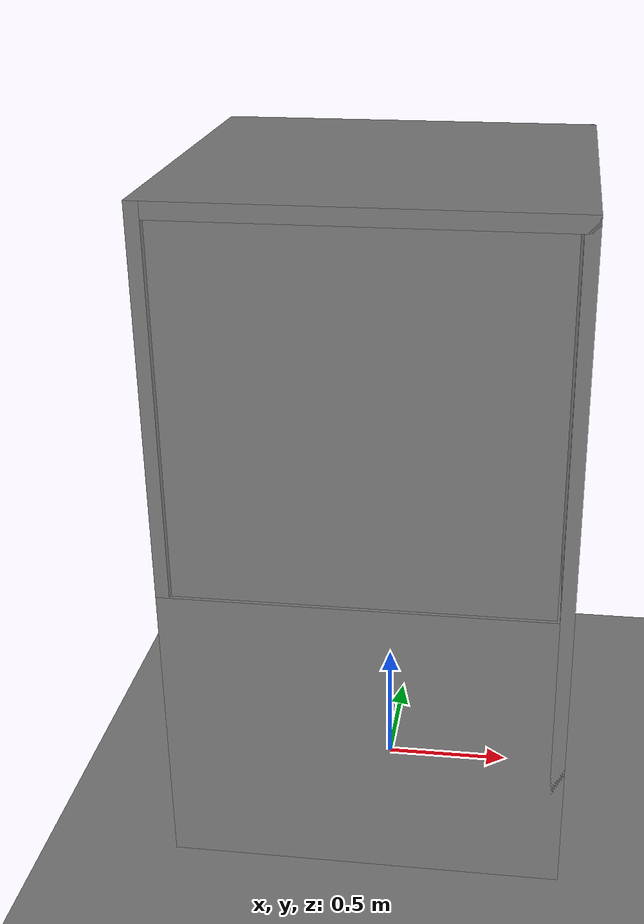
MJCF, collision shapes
<mujoco model="aic_world">
  <compiler angle="radian"/>

  <option gravity="0 0 -9.8" magnetic="5.5645e-06 2.28758e-05 -4.23884e-05"/>

  <visual>
    <headlight ambient="0 0 0" diffuse="0 0 0" specular="0 0 0"/>
  </visual>

  <default>
    <default class="world_default"/>
    <default class="cable_default">
      <joint damping="0.2"/>
    </default>
    <default class="sc_port_default">
      <geom friction="0.5 0.5"/>
    </default>
    <default class="nic_card_default">
      <geom friction="0.1 0.005 0.1"/>
    </default>
  </default>

  <extension>
    <plugin plugin="mujoco.elasticity.cable">
      <instance name="composite">
        <config key="twist" value="1e2"/>
        <config key="bend" value="4e1"/>
      </instance>
    </plugin>
  </extension>

  <asset>
    <texture type="2d" colorspace="linear" name="texture_3cfd66d2e9d880eae3d6e7923ec9058d874bf1526844466939fc4924d98ff9b9_floor_visual_Plane" file="3cfd66d2e9d880eae3d6e7923ec9058d874bf1526844466939fc4924d98ff9b9_floor_visual_b3a94635-62c15cd5e6dc70d8816b3ae0ce735df4a1737de2.png"/>
    <texture type="2d" colorspace="linear" name="texture_64e61b65f045552ba26a6ad52be1054f951feb31fe90869f7d202e8045dc22e6_sc_plug_visual_merged_0" file="64e61b65f045552ba26a6ad52be1054f951feb31fe90869f7d202e8045dc22e6_sc_plug_visual_5875f865-e008a92073d489d629a7e0a8ad8edf6cb5099f5b.png"/>
    <texture type="2d" colorspace="linear" name="texture_49bcaba7dbdb7d3142691518ed2731a8b4b7bed5e5dd55a10defd679994a8fb5_lc_plug_visual_merged_0" file="49bcaba7dbdb7d3142691518ed2731a8b4b7bed5e5dd55a10defd679994a8fb5_lc_plug_visual_03dabf32-e16878ccedad621fb18faa6179a8148c36124744.png"/>
    <texture type="2d" colorspace="linear" name="texture_4e46908e7d54f1b9f4b24d75a3e64fbc26cc8ba53b13e641c435298d0fee7478_sfp_module_visual_Body.005" file="4e46908e7d54f1b9f4b24d75a3e64fbc26cc8ba53b13e641c435298d0fee7478_sfp_module_visual_8fc63b58-70f8bbc436ea9ff3ce4f61ad23a157014f86ed54.png"/>
    <texture type="2d" colorspace="linear" name="texture_4e46908e7d54f1b9f4b24d75a3e64fbc26cc8ba53b13e641c435298d0fee7478_sfp_module_visual_Body.005_1" file="4e46908e7d54f1b9f4b24d75a3e64fbc26cc8ba53b13e641c435298d0fee7478_sfp_module_visual_1f09e86a-7b20c61a9a9c90b6cfd6c3cfd562a440aa382c7c.png"/>
    <texture type="2d" colorspace="linear" name="texture_d1b04fad6d29ff6a8ddafafe01f51e4115506104619cde448122a63197c4db36_sc_port_visual_FOA-005A_3D_v1.006" file="d1b04fad6d29ff6a8ddafafe01f51e4115506104619cde448122a63197c4db36_sc_port_visual_dde5a3d8-21f3a346f5b6de9db3bafef5d8030601544d25a0.png"/>
    <texture type="2d" colorspace="linear" name="texture_11ca22ec5bc4bf3254ee393918b3b659d90ac573596f8ddff3835610b068bcee_nic_card_visual_merged_0" file="11ca22ec5bc4bf3254ee393918b3b659d90ac573596f8ddff3835610b068bcee_nic_card_visual_45ced356-64201023db6ee43f7b49523cfdd1043cb657fcc1.png"/>
    <texture type="2d" colorspace="linear" name="texture_11ca22ec5bc4bf3254ee393918b3b659d90ac573596f8ddff3835610b068bcee_nic_card_visual_merged_1" file="11ca22ec5bc4bf3254ee393918b3b659d90ac573596f8ddff3835610b068bcee_nic_card_visual_39dce63a-e258973d213b4c8c726a76db33067b7571a9f892.png"/>
    <material name="material_d3a88c2c9b67693c0b83a473c736f84a8297c1036d4dce4e6c4e840aec16baa7_enclosure_visual_V1014952.001" class="world_default" shininess="30" rgba="0.290196 0.290196 0.290196 1"/>
    <material name="material_d3a88c2c9b67693c0b83a473c736f84a8297c1036d4dce4e6c4e840aec16baa7_enclosure_visual_V1014952.001_1" class="world_default" shininess="30" rgba="0.129412 0.129412 0.133333 1"/>
    <material name="material_d3a88c2c9b67693c0b83a473c736f84a8297c1036d4dce4e6c4e840aec16baa7_light_visual_Plane.001" class="world_default" shininess="30" rgba="0.5 0.5 0.5 1"/>
    <material name="material_3cfd66d2e9d880eae3d6e7923ec9058d874bf1526844466939fc4924d98ff9b9_floor_visual_Plane" class="world_default" texture="texture_3cfd66d2e9d880eae3d6e7923ec9058d874bf1526844466939fc4924d98ff9b9_floor_visual_Plane" shininess="30" rgba="0.5 0.5 0.5 1"/>
    <material name="material_3cfd66d2e9d880eae3d6e7923ec9058d874bf1526844466939fc4924d98ff9b9_walls_visual_Curve.001" class="world_default" shininess="30" rgba="0.0196078 0.0196078 0.0196078 1"/>
    <material name="material_3cfd66d2e9d880eae3d6e7923ec9058d874bf1526844466939fc4924d98ff9b9_walls_visual_merged_1" class="world_default" shininess="30" rgba="0.262745 0.262745 0.262745 1"/>
    <material name="material_3cfd66d2e9d880eae3d6e7923ec9058d874bf1526844466939fc4924d98ff9b9_walls_visual_Plane.003_1" class="world_default" shininess="30" rgba="0.8 0.8 0.8 1"/>
    <material name="material_3cfd66d2e9d880eae3d6e7923ec9058d874bf1526844466939fc4924d98ff9b9_walls_visual_Plane.002" class="world_default" shininess="30" rgba="0.207843 0.207843 0.207843 1"/>
    <material name="material_64e61b65f045552ba26a6ad52be1054f951feb31fe90869f7d202e8045dc22e6_sc_plug_visual_merged_0" class="world_default" texture="texture_64e61b65f045552ba26a6ad52be1054f951feb31fe90869f7d202e8045dc22e6_sc_plug_visual_merged_0" shininess="30" rgba="0.5 0.5 0.5 1"/>
    <material name="material_49bcaba7dbdb7d3142691518ed2731a8b4b7bed5e5dd55a10defd679994a8fb5_lc_plug_visual_merged_0" class="world_default" texture="texture_49bcaba7dbdb7d3142691518ed2731a8b4b7bed5e5dd55a10defd679994a8fb5_lc_plug_visual_merged_0" shininess="30" rgba="0.5 0.5 0.5 1"/>
    <material name="material_4e46908e7d54f1b9f4b24d75a3e64fbc26cc8ba53b13e641c435298d0fee7478_sfp_module_visual_Body.005" class="world_default" texture="texture_4e46908e7d54f1b9f4b24d75a3e64fbc26cc8ba53b13e641c435298d0fee7478_sfp_module_visual_Body.005" shininess="30" rgba="0.5 0.5 0.5 1"/>
    <material name="material_4e46908e7d54f1b9f4b24d75a3e64fbc26cc8ba53b13e641c435298d0fee7478_sfp_module_visual_Body.005_1" class="world_default" texture="texture_4e46908e7d54f1b9f4b24d75a3e64fbc26cc8ba53b13e641c435298d0fee7478_sfp_module_visual_Body.005_1" shininess="30" rgba="0.5 0.5 0.5 1"/>
    <material name="material_5d10b2ccf9ef8263b111a7e55a6b5dcf9c2d68105c468901e801678ea93c82ec_base_visual_ISO_4762_-_M3_x_8.019" class="world_default" shininess="30" rgba="0.0352941 0.0352941 0.0313726 1"/>
    <material name="material_5d10b2ccf9ef8263b111a7e55a6b5dcf9c2d68105c468901e801678ea93c82ec_base_visual_ISO_4762_-_M3_x_8.019_1" class="world_default" shininess="30" rgba="0.0313726 0.0313726 0.0313726 1"/>
    <material name="material_5d10b2ccf9ef8263b111a7e55a6b5dcf9c2d68105c468901e801678ea93c82ec_base_visual_ISO_4762_-_M3_x_8.019_2" class="world_default" shininess="30" rgba="0.215686 0 0.215686 1"/>
    <material name="material_39fd7e74cdb4d52c9d01c8de21359f749ea1bfe7a1f2136fc19f2d9a98855c02_sc_mount_visual_ISO_4762_-_M2_x_8.040" class="world_default" shininess="30" rgba="0.0352941 0.0352941 0.0313726 1"/>
    <material name="material_39fd7e74cdb4d52c9d01c8de21359f749ea1bfe7a1f2136fc19f2d9a98855c02_sc_mount_visual_ISO_4762_-_M2_x_8.040_1" class="world_default" shininess="30" rgba="0.0313726 0.0313726 0.0313726 1"/>
    <material name="material_a868460f64b676f0077827b48115680161bdef32d67cb4691cdc6946bb896345_sfp_mount_visual_ISO_4762_-_M2_x_8.011" class="world_default" shininess="30" rgba="0.0313726 0.0313726 0.0313726 1"/>
    <material name="material_a868460f64b676f0077827b48115680161bdef32d67cb4691cdc6946bb896345_sfp_mount_visual_ISO_4762_-_M2_x_8.011_1" class="world_default" shininess="30" rgba="0.0352941 0.0352941 0.0313726 1"/>
    <material name="material_d1b04fad6d29ff6a8ddafafe01f51e4115506104619cde448122a63197c4db36_sc_port_visual_FOA-005A_3D_v1.006" class="world_default" texture="texture_d1b04fad6d29ff6a8ddafafe01f51e4115506104619cde448122a63197c4db36_sc_port_visual_FOA-005A_3D_v1.006" shininess="30" rgba="0.5 0.5 0.5 1"/>
    <material name="material_d1b04fad6d29ff6a8ddafafe01f51e4115506104619cde448122a63197c4db36_sc_port_visual_merged_1" class="world_default" shininess="30" rgba="0.0352941 0.0352941 0.0313726 1"/>
    <material name="material_d1b04fad6d29ff6a8ddafafe01f51e4115506104619cde448122a63197c4db36_sc_port_visual_merged_2" class="world_default" shininess="30" rgba="0.0313726 0.0313726 0.0313726 1"/>
    <material name="material_11ca22ec5bc4bf3254ee393918b3b659d90ac573596f8ddff3835610b068bcee_nic_card_mount_visual_ISO_4762_-_M2_x_8.054" class="world_default" shininess="30" rgba="0.0352941 0.0352941 0.0313726 1"/>
    <material name="material_11ca22ec5bc4bf3254ee393918b3b659d90ac573596f8ddff3835610b068bcee_nic_card_mount_visual_ISO_4762_-_M2_x_8.054_1" class="world_default" shininess="30" rgba="0.0313726 0.0313726 0.0313726 1"/>
    <material name="material_11ca22ec5bc4bf3254ee393918b3b659d90ac573596f8ddff3835610b068bcee_nic_card_visual_merged_0" class="world_default" texture="texture_11ca22ec5bc4bf3254ee393918b3b659d90ac573596f8ddff3835610b068bcee_nic_card_visual_merged_0" shininess="30" rgba="0.5 0.5 0.5 1"/>
    <material name="material_11ca22ec5bc4bf3254ee393918b3b659d90ac573596f8ddff3835610b068bcee_nic_card_visual_merged_1" class="world_default" texture="texture_11ca22ec5bc4bf3254ee393918b3b659d90ac573596f8ddff3835610b068bcee_nic_card_visual_merged_1" shininess="30" rgba="0.5 0.5 0.5 1"/>
    <material name="material_11ca22ec5bc4bf3254ee393918b3b659d90ac573596f8ddff3835610b068bcee_nic_card_visual_Plane.029" class="world_default" shininess="30" rgba="0.0235294 0.0392157 0.0117647 1"/>
    <material name="material_11ca22ec5bc4bf3254ee393918b3b659d90ac573596f8ddff3835610b068bcee_nic_card_visual_Cube.007" class="world_default" shininess="30" rgba="0 0 0 1"/>
    <mesh name="d3a88c2c9b67693c0b83a473c736f84a8297c1036d4dce4e6c4e840aec16baa7_enclosure_visual_V1014952.001" class="world_default" content_type="model/obj" file="d3a88c2c9b67693c0b83a473c736f84a8297c1036d4dce4e6c4e840aec16baa7_enclosure_visual_V1014952.001-c990efe7b9dfe87aa065fd6eb3960ce051ae2aef.obj" inertia="shell"/>
    <mesh name="d3a88c2c9b67693c0b83a473c736f84a8297c1036d4dce4e6c4e840aec16baa7_enclosure_visual_V1014952.001_1" class="world_default" content_type="model/obj" file="d3a88c2c9b67693c0b83a473c736f84a8297c1036d4dce4e6c4e840aec16baa7_enclosure_visual_V1014952.001_1-807e07de06af157c84b994a232617507a7059420.obj" inertia="shell"/>
    <mesh name="d3a88c2c9b67693c0b83a473c736f84a8297c1036d4dce4e6c4e840aec16baa7_light_visual_Plane.001" class="world_default" content_type="model/obj" file="d3a88c2c9b67693c0b83a473c736f84a8297c1036d4dce4e6c4e840aec16baa7_light_visual_Plane.001-a8a774a80bc239d73769a498eae528b206eebcb0.obj" inertia="shell"/>
    <mesh name="3cfd66d2e9d880eae3d6e7923ec9058d874bf1526844466939fc4924d98ff9b9_floor_visual_Plane" class="world_default" content_type="model/obj" file="3cfd66d2e9d880eae3d6e7923ec9058d874bf1526844466939fc4924d98ff9b9_floor_visual_Plane-4dc7f6150ad7c239769a0860a01efb2015657aea.obj" inertia="shell"/>
    <mesh name="3cfd66d2e9d880eae3d6e7923ec9058d874bf1526844466939fc4924d98ff9b9_walls_visual_Curve.001" class="world_default" content_type="model/obj" file="3cfd66d2e9d880eae3d6e7923ec9058d874bf1526844466939fc4924d98ff9b9_walls_visual_Curve.001-4d7c79ac2e958832fdb15589262141ca1b80d3a5.obj" inertia="shell"/>
    <mesh name="3cfd66d2e9d880eae3d6e7923ec9058d874bf1526844466939fc4924d98ff9b9_walls_visual_merged_1" class="world_default" content_type="model/obj" file="3cfd66d2e9d880eae3d6e7923ec9058d874bf1526844466939fc4924d98ff9b9_walls_visual_merged_1-359a22140d528747936e80bedf90e1437a177a9f.obj" inertia="shell"/>
    <mesh name="3cfd66d2e9d880eae3d6e7923ec9058d874bf1526844466939fc4924d98ff9b9_walls_visual_Plane.003_1" class="world_default" content_type="model/obj" file="3cfd66d2e9d880eae3d6e7923ec9058d874bf1526844466939fc4924d98ff9b9_walls_visual_Plane.003_1-cd05ed21fa19a2784fb772d7519abf7c31c8b85f.obj" inertia="shell"/>
    <mesh name="3cfd66d2e9d880eae3d6e7923ec9058d874bf1526844466939fc4924d98ff9b9_walls_visual_Plane.002" class="world_default" content_type="model/obj" file="3cfd66d2e9d880eae3d6e7923ec9058d874bf1526844466939fc4924d98ff9b9_walls_visual_Plane.002-ee4f781765eec46c2256d941981732d4b1857f24.obj" inertia="shell"/>
    <mesh name="64e61b65f045552ba26a6ad52be1054f951feb31fe90869f7d202e8045dc22e6_sc_plug_visual_merged_0" class="world_default" content_type="model/obj" file="64e61b65f045552ba26a6ad52be1054f951feb31fe90869f7d202e8045dc22e6_sc_plug_visual_merged_0-67f94accf247f722dd4954d7448d7956402901f2.obj" inertia="shell"/>
    <mesh name="49bcaba7dbdb7d3142691518ed2731a8b4b7bed5e5dd55a10defd679994a8fb5_lc_plug_visual_merged_0" class="world_default" content_type="model/obj" file="49bcaba7dbdb7d3142691518ed2731a8b4b7bed5e5dd55a10defd679994a8fb5_lc_plug_visual_merged_0-fdaf59710fc3cc118a7df05add4ff4205edda4ef.obj" inertia="shell"/>
    <mesh name="4e46908e7d54f1b9f4b24d75a3e64fbc26cc8ba53b13e641c435298d0fee7478_sfp_module_visual_Body.005" class="world_default" content_type="model/obj" file="4e46908e7d54f1b9f4b24d75a3e64fbc26cc8ba53b13e641c435298d0fee7478_sfp_module_visual_Body.005-f93147e1e403de321fb70c06a4b1e00f20feb9fd.obj" inertia="shell"/>
    <mesh name="4e46908e7d54f1b9f4b24d75a3e64fbc26cc8ba53b13e641c435298d0fee7478_sfp_module_visual_Body.005_1" class="world_default" content_type="model/obj" file="4e46908e7d54f1b9f4b24d75a3e64fbc26cc8ba53b13e641c435298d0fee7478_sfp_module_visual_Body.005_1-4af964a95522e2593eb6381eca4f09ef239782c7.obj" inertia="shell"/>
    <mesh name="5d10b2ccf9ef8263b111a7e55a6b5dcf9c2d68105c468901e801678ea93c82ec_base_visual_ISO_4762_-_M3_x_8.019" class="world_default" content_type="model/obj" file="5d10b2ccf9ef8263b111a7e55a6b5dcf9c2d68105c468901e801678ea93c82ec_base_visual_ISO_4762_-_M3_x_8.019-f814bb518c42769543ab6246809f3fe4af5c2b64.obj" inertia="shell"/>
    <mesh name="5d10b2ccf9ef8263b111a7e55a6b5dcf9c2d68105c468901e801678ea93c82ec_base_visual_ISO_4762_-_M3_x_8.019_1" class="world_default" content_type="model/obj" file="5d10b2ccf9ef8263b111a7e55a6b5dcf9c2d68105c468901e801678ea93c82ec_base_visual_ISO_4762_-_M3_x_8.019_1-0b276ba9910a7642121235b62d2afc47c3995782.obj" inertia="shell"/>
    <mesh name="5d10b2ccf9ef8263b111a7e55a6b5dcf9c2d68105c468901e801678ea93c82ec_base_visual_ISO_4762_-_M3_x_8.019_2" class="world_default" content_type="model/obj" file="5d10b2ccf9ef8263b111a7e55a6b5dcf9c2d68105c468901e801678ea93c82ec_base_visual_ISO_4762_-_M3_x_8.019_2-7b96569be9572803417c5650ee83c9c883b44191.obj" inertia="shell"/>
    <mesh name="39fd7e74cdb4d52c9d01c8de21359f749ea1bfe7a1f2136fc19f2d9a98855c02_sc_mount_visual_ISO_4762_-_M2_x_8.040" class="world_default" content_type="model/obj" file="39fd7e74cdb4d52c9d01c8de21359f749ea1bfe7a1f2136fc19f2d9a98855c02_sc_mount_visual_ISO_4762_-_M2_x_8.040-78687100ffd558e8f9e1624af1d7c66e544fb2b1.obj" inertia="shell"/>
    <mesh name="39fd7e74cdb4d52c9d01c8de21359f749ea1bfe7a1f2136fc19f2d9a98855c02_sc_mount_visual_ISO_4762_-_M2_x_8.040_1" class="world_default" content_type="model/obj" file="39fd7e74cdb4d52c9d01c8de21359f749ea1bfe7a1f2136fc19f2d9a98855c02_sc_mount_visual_ISO_4762_-_M2_x_8.040_1-b37e6ae2e05f8677f37dfa75affee0820ec2722c.obj" inertia="shell"/>
    <mesh name="a868460f64b676f0077827b48115680161bdef32d67cb4691cdc6946bb896345_sfp_mount_visual_ISO_4762_-_M2_x_8.011" class="world_default" content_type="model/obj" file="a868460f64b676f0077827b48115680161bdef32d67cb4691cdc6946bb896345_sfp_mount_visual_ISO_4762_-_M2_x_8.011-e79a298280ce559f60558a5df64e118c814f63e4.obj" inertia="shell"/>
    <mesh name="a868460f64b676f0077827b48115680161bdef32d67cb4691cdc6946bb896345_sfp_mount_visual_ISO_4762_-_M2_x_8.011_1" class="world_default" content_type="model/obj" file="a868460f64b676f0077827b48115680161bdef32d67cb4691cdc6946bb896345_sfp_mount_visual_ISO_4762_-_M2_x_8.011_1-3a79ef8883f6645921d3fa2c67cf381141e6ea26.obj" inertia="shell"/>
    <mesh name="d1b04fad6d29ff6a8ddafafe01f51e4115506104619cde448122a63197c4db36_sc_port_visual_FOA-005A_3D_v1.006" class="world_default" content_type="model/obj" file="d1b04fad6d29ff6a8ddafafe01f51e4115506104619cde448122a63197c4db36_sc_port_visual_FOA-005A_3D_v1.006-0690c54f8a7d5fd325c57bdd49f081ad4db184ec.obj" inertia="shell"/>
    <mesh name="d1b04fad6d29ff6a8ddafafe01f51e4115506104619cde448122a63197c4db36_sc_port_visual_merged_1" class="world_default" content_type="model/obj" file="d1b04fad6d29ff6a8ddafafe01f51e4115506104619cde448122a63197c4db36_sc_port_visual_merged_1-31aef5141da75eeb5a734da46bb7eaf48a169650.obj" inertia="shell"/>
    <mesh name="d1b04fad6d29ff6a8ddafafe01f51e4115506104619cde448122a63197c4db36_sc_port_visual_merged_2" class="world_default" content_type="model/obj" file="d1b04fad6d29ff6a8ddafafe01f51e4115506104619cde448122a63197c4db36_sc_port_visual_merged_2-a5eaa459350ec83eadeb09501472b99f6092b833.obj" inertia="shell"/>
    <mesh name="11ca22ec5bc4bf3254ee393918b3b659d90ac573596f8ddff3835610b068bcee_nic_card_mount_visual_ISO_4762_-_M2_x_8.054" class="world_default" content_type="model/obj" file="11ca22ec5bc4bf3254ee393918b3b659d90ac573596f8ddff3835610b068bcee_nic_card_mount_visual_ISO_4762_-_M2_x_8.054-865f98896565b646973302f5cc3bb20e1474682a.obj" inertia="shell"/>
    <mesh name="11ca22ec5bc4bf3254ee393918b3b659d90ac573596f8ddff3835610b068bcee_nic_card_mount_visual_ISO_4762_-_M2_x_8.054_1" class="world_default" content_type="model/obj" file="11ca22ec5bc4bf3254ee393918b3b659d90ac573596f8ddff3835610b068bcee_nic_card_mount_visual_ISO_4762_-_M2_x_8.054_1-5adcf23490bd5794ededbd17ac1064f40ca2f1d8.obj" inertia="shell"/>
    <mesh name="11ca22ec5bc4bf3254ee393918b3b659d90ac573596f8ddff3835610b068bcee_nic_card_visual_merged_0" class="world_default" content_type="model/obj" file="11ca22ec5bc4bf3254ee393918b3b659d90ac573596f8ddff3835610b068bcee_nic_card_visual_merged_0-b45f6200bfaa68e87732b114c99af8b477e66413.obj" inertia="shell"/>
    <mesh name="11ca22ec5bc4bf3254ee393918b3b659d90ac573596f8ddff3835610b068bcee_nic_card_visual_merged_1" class="world_default" content_type="model/obj" file="11ca22ec5bc4bf3254ee393918b3b659d90ac573596f8ddff3835610b068bcee_nic_card_visual_merged_1-0e349b7b61b9f4e172feb5320f1e8146f966f938.obj" inertia="shell"/>
    <mesh name="11ca22ec5bc4bf3254ee393918b3b659d90ac573596f8ddff3835610b068bcee_nic_card_visual_Plane.029" class="world_default" content_type="model/obj" file="11ca22ec5bc4bf3254ee393918b3b659d90ac573596f8ddff3835610b068bcee_nic_card_visual_Plane.029-3e628f059a97b4e803370a2b5e0abfcfac063972.obj" inertia="shell"/>
    <mesh name="11ca22ec5bc4bf3254ee393918b3b659d90ac573596f8ddff3835610b068bcee_nic_card_visual_Cube.007" class="world_default" content_type="model/obj" file="11ca22ec5bc4bf3254ee393918b3b659d90ac573596f8ddff3835610b068bcee_nic_card_visual_Cube.007-f8fbe4a2582482ceb99cb3e87bdf6d5a3daf05ec.obj" inertia="shell"/>
  </asset>

  <worldbody>
    <light name="enclosure_light" class="world_default" pos="0 0 2.5" dir="0 0 -1" intensity="0.4" range="2" attenuation="1 0.01 0.001" cutoff="114.592" exponent="0.993023" diffuse="1 1 1" specular="0.1 0.1 0.1"/>
    <light name="ceiling_01" class="world_default" pos="2 2 6" dir="0 0 -1" intensity="2" range="9" castshadow="false" attenuation="1 0.01 0.001" cutoff="360" diffuse="1 1 1" specular="0.1 0.1 0.1"/>
    <light name="ceiling_02" class="world_default" pos="-2 -2 6" dir="0 0 -1" intensity="2" range="9" castshadow="false" attenuation="1 0.01 0.001" cutoff="360" diffuse="1 1 1" specular="0.1 0.1 0.1"/>
    <body name="enclosure_link">
      <inertial pos="0 0 0" mass="1" diaginertia="1 1 1"/>
      <geom name="v1015026001_collider_box" class="world_default" size="0.75 0.569492 0.75" pos="-0.010998 0.009283 0.569706" quat="-1.22475e-07 1.22474e-07 -0.707107 -0.707107" type="box" group="3"/>
      <geom name="v1015028001_collider_box" class="world_default" size="0.0254 0.0254 1.25" pos="0.713602 0.733883 1.3292" quat="1.73205e-07 0 0 -1" type="box" group="3"/>
      <geom name="v1015013001_collider_box" class="world_default" size="0.0304 0.75 0.75" pos="-0.010998 0.009283 2.5488" quat="0.707107 0 -0.707107 0" type="box" group="3"/>
      <geom name="v1015027_collider_box" class="world_default" size="0.0254 0.0254 1.25" pos="-0.735598 0.733883 1.3292" quat="1.73205e-07 0 0 -1" type="box" group="3"/>
      <geom name="v1015029_collider_box" class="world_default" size="0.0254 0.0254 1.25" pos="-0.735598 -0.715317 1.3292" quat="0 1.73205e-07 -1 -1.73205e-07" type="box" group="3"/>
      <geom name="v1015030_collider_box" class="world_default" size="0.0254 0.0254 1.25" pos="0.713602 -0.715317 1.3292" quat="1.73205e-07 0 0 -1" type="box" group="3"/>
      <geom name="enclosure_visual" class="world_default" type="mesh" contype="0" conaffinity="0" material="material_d3a88c2c9b67693c0b83a473c736f84a8297c1036d4dce4e6c4e840aec16baa7_enclosure_visual_V1014952.001" mesh="d3a88c2c9b67693c0b83a473c736f84a8297c1036d4dce4e6c4e840aec16baa7_enclosure_visual_V1014952.001"/>
      <geom name="enclosure_visual_0" class="world_default" type="mesh" contype="0" conaffinity="0" material="material_d3a88c2c9b67693c0b83a473c736f84a8297c1036d4dce4e6c4e840aec16baa7_enclosure_visual_V1014952.001_1" mesh="d3a88c2c9b67693c0b83a473c736f84a8297c1036d4dce4e6c4e840aec16baa7_enclosure_visual_V1014952.001_1"/>
      <geom name="light_visual" class="world_default" type="mesh" contype="0" conaffinity="0" material="material_d3a88c2c9b67693c0b83a473c736f84a8297c1036d4dce4e6c4e840aec16baa7_light_visual_Plane.001" mesh="d3a88c2c9b67693c0b83a473c736f84a8297c1036d4dce4e6c4e840aec16baa7_light_visual_Plane.001"/>
    </body>
    <body name="enclosure_walls_link">
      <inertial pos="0 0 0" mass="1" diaginertia="1 1 1"/>
      <geom name="v1015062006_collider_box" class="world_default" size="0.0250005 0.6796 0.6892" pos="-0.010998 0.734284 1.8288" quat="0.5 0.5 -0.5 -0.5" type="box" group="3"/>
      <geom name="v1015062005_collider_box" class="world_default" size="0.6892 0.6796 0.025" pos="-0.735998 0.009283 1.8288" quat="0.5 0.5 -0.5 -0.5" type="box" group="3"/>
      <geom name="v1015062007_collider_box" class="world_default" size="0.025 0.6846 0.6892" pos="-0.010998 -0.715717 1.8338" quat="0.5 0.5 -0.5 -0.5" type="box" group="3"/>
      <geom name="v1015062008_collider_box" class="world_default" size="0.6892 0.6846 0.025" pos="0.714002 0.009283 1.8338" quat="0.5 0.5 -0.5 -0.5" type="box" group="3"/>
    </body>
    <body name="floor_link">
      <inertial pos="0 0 0" mass="1" diaginertia="1 1 1"/>
      <geom name="floor_cylinder" class="world_default" size="5 5 1" type="plane" group="3"/>
      <geom name="floor_visual" class="world_default" type="mesh" contype="0" conaffinity="0" material="material_3cfd66d2e9d880eae3d6e7923ec9058d874bf1526844466939fc4924d98ff9b9_floor_visual_Plane" mesh="3cfd66d2e9d880eae3d6e7923ec9058d874bf1526844466939fc4924d98ff9b9_floor_visual_Plane"/>
      <geom name="walls_visual" class="world_default" type="mesh" contype="0" conaffinity="0" material="material_3cfd66d2e9d880eae3d6e7923ec9058d874bf1526844466939fc4924d98ff9b9_walls_visual_Curve.001" mesh="3cfd66d2e9d880eae3d6e7923ec9058d874bf1526844466939fc4924d98ff9b9_walls_visual_Curve.001"/>
      <geom name="walls_visual_0" class="world_default" type="mesh" contype="0" conaffinity="0" material="material_3cfd66d2e9d880eae3d6e7923ec9058d874bf1526844466939fc4924d98ff9b9_walls_visual_merged_1" mesh="3cfd66d2e9d880eae3d6e7923ec9058d874bf1526844466939fc4924d98ff9b9_walls_visual_merged_1"/>
      <geom name="walls_visual_1" class="world_default" type="mesh" contype="0" conaffinity="0" material="material_3cfd66d2e9d880eae3d6e7923ec9058d874bf1526844466939fc4924d98ff9b9_walls_visual_Plane.003_1" mesh="3cfd66d2e9d880eae3d6e7923ec9058d874bf1526844466939fc4924d98ff9b9_walls_visual_Plane.003_1"/>
      <geom name="walls_visual_2" class="world_default" type="mesh" contype="0" conaffinity="0" material="material_3cfd66d2e9d880eae3d6e7923ec9058d874bf1526844466939fc4924d98ff9b9_walls_visual_Plane.002" mesh="3cfd66d2e9d880eae3d6e7923ec9058d874bf1526844466939fc4924d98ff9b9_walls_visual_Plane.002"/>
    </body>
    <body name="cable_end_0" childclass="cable_default" pos="0.171400 0.020606 1.511889" quat="0.712741 0.312130 -0.052173 0.625982">
      <freejoint name="cable_end_0_free"/>
      <inertial pos="0 0 0" mass="0.0025" diaginertia="0.01 0.01 0.01"/>
      <geom name="base_vis" class="world_default" size="0.002" contype="0" conaffinity="0"/>
      <plugin instance="composite"/>
      <body name="cable_connection_0" pos="-2.48032e-08 2.17152e-08 -1.45797e-07" quat="0.922729 -0.0944968 -0.331446 0.172583">
        <inertial pos="0 0 0" mass="0.01" diaginertia="0.01 0.01 0.01"/>
        <joint name="joint_connection_end_0" class="world_default" pos="0 0 0" type="ball" damping="0.2"/>
        <geom name="visual_0_0" class="world_default" size="0.001 0.00180278" pos="-0.00180278 0.002 0" quat="0.676768 0.204909 0.676764 -0.204908" type="cylinder" contype="0" conaffinity="0"/>
        <geom name="visual_1_0" class="world_default" size="0.001 0.00180278" pos="-0.00180278 -0.002 0" quat="0.676768 -0.204909 0.676764 0.204908" type="cylinder" contype="0" conaffinity="0"/>
        <plugin instance="composite"/>
        <body name="link_1" pos="0.00170632 -0.00556858 -0.0232827" quat="-0.0670116 -0.276934 -0.95308 0.102252">
          <inertial pos="0 0 0" mass="0.0025" diaginertia="0.01 0.01 0.01"/>
          <joint name="joint_end_0" pos="0 0 -0.024" type="ball"/>
          <geom name="link_1_collision" size="0.002 0.018" pos="0 0 0.006" type="cylinder" group="3"/>
          <geom name="sphere_1_collision" size="0.002" pos="0 0 0.024" group="3"/>
          <geom name="link_1_vis" size="0.002 0.024" type="cylinder" contype="0" conaffinity="0"/>
          <geom name="sphere_1_vis" size="0.002" pos="0 0 0.024" contype="0" conaffinity="0"/>
          <plugin instance="composite"/>
          <body name="link_2" pos="0.0064563 -0.00759576 0.045832" quat="0.976992 0.159419 0.140563 -0.0177353">
            <inertial pos="0 0 0" mass="0.0025" diaginertia="0.01 0.01 0.01"/>
            <joint name="joint_1" pos="0 0 -0.024" type="ball"/>
            <geom name="link_2_collision" size="0.002 0.024" type="cylinder" group="3"/>
            <geom name="sphere_2_collision" size="0.002" pos="0 0 0.024" group="3"/>
            <geom name="link_2_vis" size="0.002 0.024" type="cylinder" contype="0" conaffinity="0"/>
            <geom name="sphere_2_vis" size="0.002" pos="0 0 0.024" contype="0" conaffinity="0"/>
            <plugin instance="composite"/>
            <body name="link_3" pos="0.000666041 -0.00668751 0.0470402" quat="0.98975 0.140425 0.0168223 -0.0198334">
              <inertial pos="0 0 0" mass="0.0025" diaginertia="0.01 0.01 0.01"/>
              <joint name="joint_2" pos="0 0 -0.024" type="ball"/>
              <geom name="link_3_collision" size="0.002 0.024" type="cylinder" group="3"/>
              <geom name="sphere_3_collision" size="0.002" pos="0 0 0.024" group="3"/>
              <geom name="link_3_vis" size="0.002 0.024" type="cylinder" contype="0" conaffinity="0"/>
              <geom name="sphere_3_vis" size="0.002" pos="0 0 0.024" contype="0" conaffinity="0"/>
              <plugin instance="composite"/>
              <body name="link_4" pos="-0.00201756 -0.0046759 0.0474536" quat="0.994004 0.0989623 -0.0399132 -0.0238771">
                <inertial pos="0 0 0" mass="0.0025" diaginertia="0.01 0.01 0.01"/>
                <joint name="joint_3" pos="0 0 -0.024" type="ball"/>
                <geom name="link_4_collision" size="0.002 0.024" type="cylinder" group="3"/>
                <geom name="sphere_4_collision" size="0.002" pos="0 0 0.024" group="3"/>
                <geom name="link_4_vis" size="0.002 0.024" type="cylinder" contype="0" conaffinity="0"/>
                <geom name="sphere_4_vis" size="0.002" pos="0 0 0.024" contype="0" conaffinity="0"/>
                <plugin instance="composite"/>
                <body name="link_5" pos="-0.00359934 -0.0031378 0.0475207" quat="0.994211 0.0686286 -0.0727025 -0.0393501">
                  <inertial pos="0 0 0" mass="0.0025" diaginertia="0.01 0.01 0.01"/>
                  <joint name="joint_4" pos="0 0 -0.024" type="ball"/>
                  <geom name="link_5_collision" size="0.002 0.024" type="cylinder" group="3"/>
                  <geom name="sphere_5_collision" size="0.002" pos="0 0 0.024" group="3"/>
                  <geom name="link_5_vis" size="0.002 0.024" type="cylinder" contype="0" conaffinity="0"/>
                  <geom name="sphere_5_vis" size="0.002" pos="0 0 0.024" contype="0" conaffinity="0"/>
                  <plugin instance="composite"/>
                  <body name="link_6" pos="-0.00400601 -0.00179596 0.0475953" quat="0.993829 0.0427394 -0.0813241 -0.0621514">
                    <inertial pos="0 0 0" mass="0.0025" diaginertia="0.01 0.01 0.01"/>
                    <joint name="joint_5" pos="0 0 -0.024" type="ball"/>
                    <geom name="link_6_collision" size="0.002 0.024" type="cylinder" group="3"/>
                    <geom name="sphere_6_collision" size="0.002" pos="0 0 0.024" group="3"/>
                    <geom name="link_6_vis" size="0.002 0.024" type="cylinder" contype="0" conaffinity="0"/>
                    <geom name="sphere_6_vis" size="0.002" pos="0 0 0.024" contype="0" conaffinity="0"/>
                    <plugin instance="composite"/>
                    <body name="link_7" pos="-0.00359567 -0.000736965 0.0477182" quat="0.993406 0.0217587 -0.0735419 -0.0852205">
                      <inertial pos="0 0 0" mass="0.0025" diaginertia="0.01 0.01 0.01"/>
                      <joint name="joint_6" pos="0 0 -0.024" type="ball"/>
                      <geom name="link_7_collision" size="0.002 0.024" type="cylinder" group="3"/>
                      <geom name="sphere_7_collision" size="0.002" pos="0 0 0.024" group="3"/>
                      <geom name="link_7_vis" size="0.002 0.024" type="cylinder" contype="0" conaffinity="0"/>
                      <geom name="sphere_7_vis" size="0.002" pos="0 0 0.024" contype="0" conaffinity="0"/>
                      <plugin instance="composite"/>
                      <body name="link_8" pos="-0.00255335 0.000119986 0.0478642" quat="0.993512 0.00286058 -0.0532556 -0.100445">
                        <inertial pos="0 0 0" mass="0.0025" diaginertia="0.01 0.01 0.01"/>
                        <joint name="joint_7" pos="0 0 -0.024" type="ball"/>
                        <geom name="link_8_collision" size="0.002 0.024" type="cylinder" group="3"/>
                        <geom name="sphere_8_collision" size="0.002" pos="0 0 0.024" group="3"/>
                        <geom name="link_8_vis" size="0.002 0.024" type="cylinder" contype="0" conaffinity="0"/>
                        <geom name="sphere_8_vis" size="0.002" pos="0 0 0.024" contype="0" conaffinity="0"/>
                        <plugin instance="composite"/>
                        <body name="link_9" pos="-0.00133737 0.000859059 0.0479485" quat="0.994153 -0.0149483 -0.0295699 -0.102776">
                          <inertial pos="0 0 0" mass="0.0025" diaginertia="0.01 0.01 0.01"/>
                          <joint name="joint_8" pos="0 0 -0.024" type="ball"/>
                          <geom name="link_9_collision" size="0.002 0.024" type="cylinder" group="3"/>
                          <geom name="sphere_9_collision" size="0.002" pos="0 0 0.024" group="3"/>
                          <geom name="link_9_vis" size="0.002 0.024" type="cylinder" contype="0" conaffinity="0"/>
                          <geom name="sphere_9_vis" size="0.002" pos="0 0 0.024" contype="0" conaffinity="0"/>
                          <plugin instance="composite"/>
                          <body name="link_10" pos="-0.000441179 0.00156015 0.0479454" quat="0.994979 -0.0314896 -0.0122296 -0.0942127">
                            <inertial pos="0 0 0" mass="0.0025" diaginertia="0.01 0.01 0.01"/>
                            <joint name="joint_9" pos="0 0 -0.024" type="ball"/>
                            <geom name="link_10_collision" size="0.002 0.024" type="cylinder" group="3"/>
                            <geom name="sphere_10_collision" size="0.002" pos="0 0 0.024" group="3"/>
                            <geom name="link_10_vis" size="0.002 0.024" type="cylinder" contype="0" conaffinity="0"/>
                            <geom name="sphere_10_vis" size="0.002" pos="0 0 0.024" contype="0" conaffinity="0"/>
                            <plugin instance="composite"/>
                            <body name="link_11" pos="0.00114853 0.00243771 0.0478493" quat="0.994284 -0.0528353 0.0192331 -0.0907645">
                              <inertial pos="0 0 0" mass="0.0025" diaginertia="0.01 0.01 0.01"/>
                              <joint name="joint_10" pos="0 0 -0.024" type="ball"/>
                              <geom name="link_11_collision" size="0.002 0.024" type="cylinder" group="3"/>
                              <geom name="sphere_11_collision" size="0.002" pos="0 0 0.024" group="3"/>
                              <geom name="link_11_vis" size="0.002 0.024" type="cylinder" contype="0" conaffinity="0"/>
                              <geom name="sphere_11_vis" size="0.002" pos="0 0 0.024" contype="0" conaffinity="0"/>
                              <plugin instance="composite"/>
                              <body name="link_12" pos="0.00319193 0.00397127 0.0474547" quat="0.991985 -0.0875655 0.0610639 -0.0676033">
                                <inertial pos="0 0 0" mass="0.0025" diaginertia="0.01 0.01 0.01"/>
                                <joint name="joint_11" pos="0 0 -0.024" type="ball"/>
                                <geom name="link_12_collision" size="0.002 0.024" type="cylinder" group="3"/>
                                <geom name="sphere_12_collision" size="0.002" pos="0 0 0.024" group="3"/>
                                <geom name="link_12_vis" size="0.002 0.024" type="cylinder" contype="0" conaffinity="0"/>
                                <geom name="sphere_12_vis" size="0.002" pos="0 0 0.024" contype="0" conaffinity="0"/>
                                <plugin instance="composite"/>
                                <body name="link_13" pos="0.00477094 0.00576188 0.0468049" quat="0.986645 -0.125566 0.0955868 -0.040351">
                                  <inertial pos="0 0 0" mass="0.0025" diaginertia="0.01 0.01 0.01"/>
                                  <joint name="joint_12" pos="0 0 -0.024" type="ball"/>
                                  <geom name="link_13_collision" size="0.002 0.024" type="cylinder" group="3"/>
                                  <geom name="sphere_13_collision" size="0.002" pos="0 0 0.024" group="3"/>
                                  <geom name="link_13_vis" size="0.002 0.024" type="cylinder" contype="0" conaffinity="0"/>
                                  <geom name="sphere_13_vis" size="0.002" pos="0 0 0.024" contype="0" conaffinity="0"/>
                                  <plugin instance="composite"/>
                                  <body name="link_14" pos="0.005839 0.00733455 0.0460941" quat="0.979848 -0.157594 0.122011 -0.0132488">
                                    <inertial pos="0 0 0" mass="0.0025" diaginertia="0.01 0.01 0.01"/>
                                    <joint name="joint_13" pos="0 0 -0.024" type="ball"/>
                                    <geom name="link_14_collision" size="0.002 0.024" type="cylinder" group="3"/>
                                    <geom name="sphere_14_collision" size="0.002" pos="0 0 0.024" group="3"/>
                                    <geom name="link_14_vis" size="0.002 0.024" type="cylinder" contype="0" conaffinity="0"/>
                                    <geom name="sphere_14_vis" size="0.002" pos="0 0 0.024" contype="0" conaffinity="0"/>
                                    <plugin instance="composite"/>
                                    <body name="link_15" pos="0.00648458 0.00806215 0.0456562" quat="0.975213 -0.170653 0.140422 0.0109129">
                                      <inertial pos="0 0 0" mass="0.0025" diaginertia="0.01 0.01 0.01"/>
                                      <joint name="joint_14" pos="0 0 -0.024" type="ball"/>
                                      <geom name="link_15_collision" size="0.002 0.024" type="cylinder" group="3"/>
                                      <geom name="sphere_15_collision" size="0.002" pos="0 0 0.024" group="3"/>
                                      <geom name="link_15_vis" size="0.002 0.024" type="cylinder" contype="0" conaffinity="0"/>
                                      <geom name="sphere_15_vis" size="0.002" pos="0 0 0.024" contype="0" conaffinity="0"/>
                                      <plugin instance="composite"/>
                                      <body name="link_16" pos="0.00662934 0.0075781 0.0457874" quat="0.976219 -0.157324 0.146215 0.0294472">
                                        <inertial pos="0 0 0" mass="0.0025" diaginertia="0.01 0.01 0.01"/>
                                        <joint name="joint_15" pos="0 0 -0.024" type="ball"/>
                                        <geom name="link_16_collision" size="0.002 0.024" type="cylinder" group="3"/>
                                        <geom name="sphere_16_collision" size="0.002" pos="0 0 0.024" group="3"/>
                                        <geom name="link_16_vis" size="0.002 0.024" type="cylinder" contype="0" conaffinity="0"/>
                                        <geom name="sphere_16_vis" size="0.002" pos="0 0 0.024" contype="0" conaffinity="0"/>
                                        <plugin instance="composite"/>
                                        <body name="link_17" pos="0.00635258 0.00595334 0.0463669" quat="0.981986 -0.120488 0.139748 0.0407034">
                                          <inertial pos="0 0 0" mass="0.0025" diaginertia="0.01 0.01 0.01"/>
                                          <joint name="joint_16" pos="0 0 -0.024" type="ball"/>
                                          <geom name="link_17_collision" size="0.002 0.024" type="cylinder" group="3"/>
                                          <geom name="sphere_17_collision" size="0.002" pos="0 0 0.024" group="3"/>
                                          <geom name="link_17_vis" size="0.002 0.024" type="cylinder" contype="0" conaffinity="0"/>
                                          <geom name="sphere_17_vis" size="0.002" pos="0 0 0.024" contype="0" conaffinity="0"/>
                                          <plugin instance="composite"/>
                                          <body name="link_18" pos="0.00575653 0.003482 0.047038" quat="0.988962 -0.06784 0.124269 0.0436973">
                                            <inertial pos="0 0 0" mass="0.0025" diaginertia="0.01 0.01 0.01"/>
                                            <joint name="joint_17" pos="0 0 -0.024" type="ball"/>
                                            <geom name="link_18_collision" size="0.002 0.024" type="cylinder" group="3"/>
                                            <geom name="sphere_18_collision" size="0.002" pos="0 0 0.024" group="3"/>
                                            <geom name="link_18_vis" size="0.002 0.024" type="cylinder" contype="0" conaffinity="0"/>
                                            <geom name="sphere_18_vis" size="0.002" pos="0 0 0.024" contype="0" conaffinity="0"/>
                                            <plugin instance="composite"/>
                                            <body name="link_19" pos="0.00550013 0.00141785 0.0473194" quat="0.992157 -0.0253624 0.116454 0.0376818">
                                              <inertial pos="0 0 0" mass="0.0025" diaginertia="0.01 0.01 0.01"/>
                                              <joint name="joint_18" pos="0 0 -0.024" type="ball"/>
                                              <geom name="link_19_collision" size="0.002 0.024" type="cylinder" group="3"/>
                                              <geom name="sphere_19_collision" size="0.002" pos="0 0 0.024" group="3"/>
                                              <geom name="link_19_vis" size="0.002 0.024" type="cylinder" contype="0" conaffinity="0"/>
                                              <geom name="sphere_19_vis" size="0.002" pos="0 0 0.024" contype="0" conaffinity="0"/>
                                              <plugin instance="composite"/>
                                              <body name="link_20" pos="0.00534656 -0.00101358 0.0473769" quat="0.993097 0.0243171 0.111486 0.027151">
                                                <inertial pos="0 0 0" mass="0.0025" diaginertia="0.01 0.01 0.01"/>
                                                <joint name="joint_19" pos="0 0 -0.024" type="ball"/>
                                                <geom name="link_20_collision" size="0.002 0.024" type="cylinder" group="3"/>
                                                <geom name="sphere_20_collision" size="0.002" pos="0 0 0.024" group="3"/>
                                                <geom name="link_20_vis" size="0.002 0.024" type="cylinder" contype="0" conaffinity="0"/>
                                                <geom name="sphere_20_vis" size="0.002" pos="0 0 0.024" contype="0" conaffinity="0"/>
                                                <plugin instance="composite"/>
                                                <body name="cable_connection_1" pos="1.18118e-06 -3.36725e-07 0.0240001" quat="0.773544 0.0588014 -0.629752 -0.039807">
                                                  <inertial pos="0 0 0" mass="0.01" diaginertia="4e-4 4e-4 4e-4"/>
                                                  <joint name="joint_connection_end_1" class="world_default" pos="0 0 0" type="ball"/>
                                                  <geom name="collision_0" class="world_default" size="0.001 0.00367636" pos="0.00367636 -0.00425 0" quat="0.673802 0.214463 0.673798 -0.214461" type="cylinder" group="3"/>
                                                  <geom name="collision_1" class="world_default" size="0.001 0.00367636" pos="0.00367636 0.00425 0" quat="0.673802 -0.214463 0.673798 0.214461" type="cylinder" group="3"/>
                                                  <geom name="visual_0" class="world_default" size="0.001 0.00367636" pos="0.00367636 -0.00425 0" quat="0.673802 0.214463 0.673798 -0.214461" type="cylinder" contype="0" conaffinity="0"/>
                                                  <geom name="visual_1" class="world_default" size="0.001 0.00367636" pos="0.00367636 0.00425 0" quat="0.673802 -0.214463 0.673798 0.214461" type="cylinder" contype="0" conaffinity="0"/>
                                                  <plugin instance="composite"/>
                                                  <body name="sc_plug_link" pos="0.0520001 -2.50452e-10 -3.85925e-08" quat="1 -9.69236e-08 -4.66151e-08 -3.51934e-09">
                                                    <inertial pos="-0.0113552 5.95326e-05 9.66547e-06" quat="0.000666424 0.706845 -0.000660251 0.707368" mass="0.04" diaginertia="8.92011e-06 7.22349e-06 2.15571e-06"/>
                                                    <geom name="housing blue_predeterminado005_collider_box" class="world_default" size="0.006861 0.0045 0.00365" pos="0.002539 0.006344 4e-06" type="box" group="3"/>
                                                    <geom name="housing blue_predeterminado005_collider_box.001" class="world_default" size="0.006861 0.0045 0.00365" pos="0.002539 -0.006344 4e-06" type="box" group="3"/>
                                                    <geom name="cube002_collider_box" class="world_default" size="0.006275 0.0125 0.00505" pos="-0.010291 0 0" type="box" group="3"/>
                                                    <geom name="cylinder011_collider_cylinder" class="world_default" size="0.0029 0.014605" pos="-0.031147 -0.00635 0" quat="0.707107 0 0.707107 0" type="cylinder" group="3"/>
                                                    <geom name="cylinder005_collider_cylinder" class="world_default" size="0.0029 0.015799" pos="-0.029953 0.00635 0" quat="0.707107 0 0.707107 0" type="cylinder" group="3"/>
                                                    <geom name="ferula_predeterminado005_collider_cylinder" class="world_default" size="0.00125 0.007" pos="0.00465 -0.00635 0" quat="0.707107 0 0.707107 0" type="cylinder" group="3"/>
                                                    <geom name="ferula_predeterminado003_collider_cylinder" class="world_default" size="0.00125 0.007" pos="0.00465 0.00635 0" quat="0.707107 0 0.707107 0" type="cylinder" group="3"/>
                                                    <geom name="side_box_collision" class="world_default" size="0.002125 0.00081 0.0005" pos="0.00146 -0.00632 0.0042" type="box" group="3"/>
                                                    <geom name="side_box_collision_2" class="world_default" size="0.002125 0.00081 0.0005" pos="0.00146 0.00632 0.0042" type="box" group="3"/>
                                                    <geom name="sc_plug_visual" class="world_default" type="mesh" contype="0" conaffinity="0" material="material_64e61b65f045552ba26a6ad52be1054f951feb31fe90869f7d202e8045dc22e6_sc_plug_visual_merged_0" mesh="64e61b65f045552ba26a6ad52be1054f951feb31fe90869f7d202e8045dc22e6_sc_plug_visual_merged_0"/>
                                                    <plugin instance="composite"/>
                                                    <body name="sc_tip_link" pos="0.01165 -3.5659e-08 1.72361e-07" quat="0.499998 -0.5 0.500001 -0.5">
                                                      <inertial pos="0 0 0" mass="0.001" diaginertia="1e-06 1e-06 1e-06"/>
                                                    </body>
                                                  </body>
                                                </body>
                                              </body>
                                            </body>
                                          </body>
                                        </body>
                                      </body>
                                    </body>
                                  </body>
                                </body>
                              </body>
                            </body>
                          </body>
                        </body>
                      </body>
                    </body>
                  </body>
                </body>
              </body>
            </body>
          </body>
        </body>
        <body name="lc_plug_link" pos="-0.041 5.02752e-09 2.98166e-09" quat="0.707109 -1.79818e-08 5.68286e-08 0.707105">
          <inertial pos="0 0.0197 0" quat="0 0.707107 0 0.707107" mass="0.01" diaginertia="1.06153e-07 9.96094e-08 8.49658e-09"/>
          <geom name="cylinder001_collider_cylinder.001" class="world_default" size="0.000625 0.001502" pos="0.003125 0.0197 0" quat="0.707107 0.707107 0 0" type="cylinder" group="3"/>
          <geom name="cylinder_collider_cylinder.001" class="world_default" size="0.000625 0.001502" pos="-0.003125 0.0197 0" quat="0.707107 0.707107 0 0" type="cylinder" group="3"/>
          <geom name="lc_plug_visual" class="world_default" type="mesh" contype="0" conaffinity="0" material="material_49bcaba7dbdb7d3142691518ed2731a8b4b7bed5e5dd55a10defd679994a8fb5_lc_plug_visual_merged_0" mesh="49bcaba7dbdb7d3142691518ed2731a8b4b7bed5e5dd55a10defd679994a8fb5_lc_plug_visual_merged_0"/>
          <body name="sfp_module_link" pos="5.84077e-09 0.0384 2.64054e-08" quat="1.60451e-08 1 -1.2485e-06 -1.38325e-06">
            <inertial pos="0.00024115 0.00702224 0.000553372" quat="0.510037 0.497012 -0.483415 0.50907" mass="0.02" diaginertia="3.07513e-06 2.81054e-06 5.69919e-07"/>
            <geom name="port_collider_box.008" class="world_default" size="0.00071 0.000503 0.0064415" pos="-0.00571 0.018813 -0.003546" quat="0.707107 0.707107 0 0" type="box" group="3"/>
            <geom name="port_collider_box.009" class="world_default" size="0.00071 0.000503 0.0064415" pos="0.00571 0.018813 -0.003546" quat="0.707107 0.707107 0 0" type="box" group="3"/>
            <geom name="body_collider_box" class="world_default" size="0.006875 0.02365 0.0003945" pos="0 0.001 0.00383" type="box" group="3"/>
            <geom name="body_collider_box.001" class="world_default" size="0.006875 0.02365 8.9e-05" pos="0 0.001 -0.004138" type="box" group="3"/>
            <geom name="body_collider_box.002" class="world_default" size="0.000287 0.02365 0.004225" pos="-0.006588 0.001 0" type="box" group="3"/>
            <geom name="body_collider_box.003" class="world_default" size="0.0004055 0.02365 0.004225" pos="0.00647 0.001 0" type="box" group="3"/>
            <geom name="port_collider_box.010" class="world_default" size="0.00642 0.0038815 0.0058645" pos="0 0.01229 0.000119" quat="0.707107 0.707107 0 0" type="box" group="3"/>
            <geom name="port_collider_box002_collider_box" class="world_default" size="0.00642 0.0002045 0.0008005" pos="0 0.024453 -0.004254" quat="0.707107 0.707107 0 0" type="box" group="3"/>
            <geom name="port_collider_box.011" class="world_default" size="0.00125 0.000503 0.0064415" pos="0 0.018813 -0.003546" quat="0.707107 0.707107 0 0" type="box" group="3"/>
            <geom name="sfp_module_visual" class="world_default" type="mesh" contype="0" conaffinity="0" material="material_4e46908e7d54f1b9f4b24d75a3e64fbc26cc8ba53b13e641c435298d0fee7478_sfp_module_visual_Body.005" mesh="4e46908e7d54f1b9f4b24d75a3e64fbc26cc8ba53b13e641c435298d0fee7478_sfp_module_visual_Body.005"/>
            <geom name="sfp_module_visual_0" class="world_default" type="mesh" contype="0" conaffinity="0" material="material_4e46908e7d54f1b9f4b24d75a3e64fbc26cc8ba53b13e641c435298d0fee7478_sfp_module_visual_Body.005_1" mesh="4e46908e7d54f1b9f4b24d75a3e64fbc26cc8ba53b13e641c435298d0fee7478_sfp_module_visual_Body.005_1"/>
            <body name="sfp_tip_link" pos="4.1719e-09 -0.02365 5.80744e-09" quat="0.707105 0.707108 4.21739e-08 -4.24679e-08">
              <inertial pos="0 0 0" mass="0.001" diaginertia="1e-06 1e-06 1e-06"/>
              <geom name="contact_collision" class="world_default" size="0.006875 0.0021125 0.0005" pos="0 0.0021125 -0.0005" type="box" group="3"/>
              <geom name="non_contact_collision" class="world_default" size="0.006875 0.0021125 0.0005" pos="0 -0.0021125 -0.0005" type="box" group="3"/>
            </body>
          </body>
        </body>
      </body>
    </body>
    <body name="task_board_base_link" pos="0.15 -0.2 1.14" quat="4.63151e-05 -5.13589e-10 -1.29702e-09 1">
      <inertial pos="0.00298077 -0.00408654 0.000423077" quat="0.331065 0.606837 -0.300201 0.657285" mass="5.2" diaginertia="0.105451 0.105385 0.102065"/>
      <geom name="task_board_base_link_fixed_joint_lump__v1015083001_collider_box_left_collision" class="world_default" size="0.15 0.114 0.0045" pos="0 -0.1 0.0075" type="box" group="3"/>
      <geom name="task_board_base_link_fixed_joint_lump__v1015083001_collider_right_collision_1" class="world_default" size="0.15 0.0635 0.0045" pos="0 0.149 0.0075" type="box" group="3"/>
      <geom name="task_board_base_link_fixed_joint_lump__v1015083001_collider_mid_collision_2" class="world_default" size="0.07 0.006 0.0045" pos="-0.075 0.05 0.0075" type="box" group="3"/>
      <geom name="task_board_base_link_fixed_joint_lump__v1015083001_collider_bottom_collision_3" class="world_default" size="0.0825 0.2125 0.0045" pos="0.068 0 0.0075" type="box" group="3"/>
      <geom name="task_board_base_link_fixed_joint_lump__v1015083001_collider_top_collision_4" class="world_default" size="0.0075 0.2125 0.0045" pos="-0.143 0 0.0075" type="box" group="3"/>
      <geom name="task_board_base_link_fixed_joint_lump__v1015079011_collider_box_collision_5" class="world_default" size="0.0088735 0.007 0.0025" pos="0.139002 -0.10625 0.0145" type="box" group="3"/>
      <geom name="task_board_base_link_fixed_joint_lump__v1015079011_collider_box.001_collision_6" class="world_default" size="0.012906 0.0016 0.0068995" pos="0.122568 -0.11165 0.025451" quat="0.92388 0 0.382683 0" type="box" group="3"/>
      <geom name="task_board_base_link_fixed_joint_lump__v1015079011_collider_box.002_collision_7" class="world_default" size="0.012906 0.00115 0.0068995" pos="0.122568 -0.1004 0.025451" quat="0.92388 0 0.382683 0" type="box" group="3"/>
      <geom name="task_board_base_link_fixed_joint_lump__v1015079011_collider_box003_collider_box_collision_8" class="world_default" size="0.001 0.007 0.0068995" pos="0.11415 -0.10625 0.03387" quat="0.92388 0 0.382683 0" type="box" group="3"/>
      <geom name="task_board_base_link_fixed_joint_lump__v1015079011_collider_box003_collider_box.001_collision_9" class="world_default" size="0.000921 0.007 0.0068995" pos="0.131064 -0.10625 0.016956" quat="0.92388 0 0.382683 0" type="box" group="3"/>
      <geom name="task_board_base_link_fixed_joint_lump__v1015079011_collider_box003_collider_box.002_collision_10" class="world_default" size="0.0124785 0.007 0.0025" pos="0.109506 -0.10625 0.0145" type="box" group="3"/>
      <geom name="task_board_base_link_fixed_joint_lump__v1015079011_collider_box003_collider_box.003_collision_11" class="world_default" size="0.012906 0.007 0.0006195" pos="0.117774 -0.10625 0.020656" quat="0.92388 0 0.382683 0" type="box" group="3"/>
      <geom name="task_board_base_link_fixed_joint_lump__v1015079011_collider_box003_collider_box.004_collision_12" class="world_default" size="0.0011105 0.007 0.0046245" pos="0.135389 -0.10625 0.016624" type="box" group="3"/>
      <geom name="task_board_base_link_fixed_joint_lump__v1015079011_collider_box003_collider_box004_collider_box_collision_13" class="world_default" size="0.001045 0.007 0.008711" pos="0.109545 -0.10625 0.020711" type="box" group="3"/>
      <geom name="task_board_base_link_fixed_joint_lump__iso_4762_m2_x_8072_collider_box_collision_14" class="world_default" size="0.0147285 0.008875 0.0025" pos="0.088272 -0.10625 0.0125" type="box" group="3"/>
      <geom name="task_board_base_link_fixed_joint_lump__iso_4762_m2_x_8072_collider_box_001_collision_15" class="world_default" size="0.0192665 0.008875 0.000864" pos="0.071366 -0.10625 0.027144" quat="0.92388 0 -0.382683 0" type="box" group="3"/>
      <geom name="task_board_base_link_fixed_joint_lump__iso_4762_m2_x_8072_collider_box_002_collision_16" class="world_default" size="0.0137425 0.008875 0.001844" pos="0.083636 -0.10625 0.022684" quat="0.92388 0 -0.382683 0" type="box" group="3"/>
      <geom name="task_board_base_link_fixed_joint_lump__iso_4762_m2_x_8072_collider_box_003_collision_17" class="world_default" size="0.0180555 0.0011525 0.005478" pos="0.076242 -0.098527 0.023979" quat="0.92388 0 -0.382683 0" type="box" group="3"/>
      <geom name="task_board_base_link_fixed_joint_lump__iso_4762_m2_x_8072_collider_box_004_collision_18" class="world_default" size="0.0180555 0.0009375 0.005815" pos="0.076003 -0.114188 0.024217" quat="0.92388 0 -0.382683 0" type="box" group="3"/>
      <geom name="task_board_base_link_fixed_joint_lump__iso_4762_m2_x_8072_collider_box_005_collision_19" class="world_default" size="0.002532 0.008875 0.005815" pos="0.065017 -0.10625 0.013231" quat="0.92388 0 -0.382683 0" type="box" group="3"/>
      <geom name="task_board_base_link_fixed_joint_lump__iso_4762_m2_x_8072_collider_box_006_collision_20" class="world_default" size="0.0071855 0.008875 0.0025" pos="0.0592 -0.10625 0.0125" type="box" group="3"/>
      <geom name="task_board_base_link_fixed_joint_lump__iso_4762_m2_x_8072_collider_box_007_collision_21" class="world_default" size="0.0024465 0.008875 0.0083775" pos="0.091553 -0.10625 0.021771" type="box" group="3"/>
      <geom name="task_board_base_link_fixed_joint_lump__base_visual_visual" class="world_default" type="mesh" contype="0" conaffinity="0" material="material_5d10b2ccf9ef8263b111a7e55a6b5dcf9c2d68105c468901e801678ea93c82ec_base_visual_ISO_4762_-_M3_x_8.019" mesh="5d10b2ccf9ef8263b111a7e55a6b5dcf9c2d68105c468901e801678ea93c82ec_base_visual_ISO_4762_-_M3_x_8.019"/>
      <geom name="task_board_base_link_fixed_joint_lump__base_visual_visual_0" class="world_default" type="mesh" contype="0" conaffinity="0" material="material_5d10b2ccf9ef8263b111a7e55a6b5dcf9c2d68105c468901e801678ea93c82ec_base_visual_ISO_4762_-_M3_x_8.019_1" mesh="5d10b2ccf9ef8263b111a7e55a6b5dcf9c2d68105c468901e801678ea93c82ec_base_visual_ISO_4762_-_M3_x_8.019_1"/>
      <geom name="task_board_base_link_fixed_joint_lump__base_visual_visual_1" class="world_default" type="mesh" contype="0" conaffinity="0" material="material_5d10b2ccf9ef8263b111a7e55a6b5dcf9c2d68105c468901e801678ea93c82ec_base_visual_ISO_4762_-_M3_x_8.019_2" mesh="5d10b2ccf9ef8263b111a7e55a6b5dcf9c2d68105c468901e801678ea93c82ec_base_visual_ISO_4762_-_M3_x_8.019_2"/>
      <geom name="task_board_base_link_fixed_joint_lump__sc_mount_visual_visual_1" class="world_default" pos="0.1 -0.10625 0.012" quat="1 0 0 0" type="mesh" contype="0" conaffinity="0" material="material_39fd7e74cdb4d52c9d01c8de21359f749ea1bfe7a1f2136fc19f2d9a98855c02_sc_mount_visual_ISO_4762_-_M2_x_8.040" mesh="39fd7e74cdb4d52c9d01c8de21359f749ea1bfe7a1f2136fc19f2d9a98855c02_sc_mount_visual_ISO_4762_-_M2_x_8.040"/>
      <geom name="task_board_base_link_fixed_joint_lump__sc_mount_visual_visual_1_0" class="world_default" pos="0.1 -0.10625 0.012" quat="1 0 0 0" type="mesh" contype="0" conaffinity="0" material="material_39fd7e74cdb4d52c9d01c8de21359f749ea1bfe7a1f2136fc19f2d9a98855c02_sc_mount_visual_ISO_4762_-_M2_x_8.040_1" mesh="39fd7e74cdb4d52c9d01c8de21359f749ea1bfe7a1f2136fc19f2d9a98855c02_sc_mount_visual_ISO_4762_-_M2_x_8.040_1"/>
      <geom name="task_board_base_link_fixed_joint_lump__sfp_mount_visual_visual_2" class="world_default" pos="0.055 -0.10625 0.01" quat="1 0 0 0" type="mesh" contype="0" conaffinity="0" material="material_a868460f64b676f0077827b48115680161bdef32d67cb4691cdc6946bb896345_sfp_mount_visual_ISO_4762_-_M2_x_8.011" mesh="a868460f64b676f0077827b48115680161bdef32d67cb4691cdc6946bb896345_sfp_mount_visual_ISO_4762_-_M2_x_8.011"/>
      <geom name="task_board_base_link_fixed_joint_lump__sfp_mount_visual_visual_2_0" class="world_default" pos="0.055 -0.10625 0.01" quat="1 0 0 0" type="mesh" contype="0" conaffinity="0" material="material_a868460f64b676f0077827b48115680161bdef32d67cb4691cdc6946bb896345_sfp_mount_visual_ISO_4762_-_M2_x_8.011_1" mesh="a868460f64b676f0077827b48115680161bdef32d67cb4691cdc6946bb896345_sfp_mount_visual_ISO_4762_-_M2_x_8.011_1"/>
      <body name="sc_port_0::sc_port_link" childclass="sc_port_default" pos="-0.075 0.0295 0.0165" quat="0.500398 0.5 0.499602 0.5">
        <inertial pos="0 -0.000889761 9.34069e-05" quat="-0.00100992 0.707106 -0.00100992 0.707106" mass="0.04" diaginertia="6.36325e-06 5.19944e-06 1.9926e-06"/>
        <geom name="cube_collider_box" class="world_default" size="0.0009685 0.013716 0.00465" pos="0.011922 0 0" type="box" group="3"/>
        <geom name="cube_collider_box.001" class="world_default" size="0.0128905 0.0054 0.000425" pos="0 0 0.004225" type="box" group="3"/>
        <geom name="cube_collider_box_mid" class="world_default" size="0.00515 0.013716 0.000425" pos="0 0 0.004225" type="box" group="3"/>
        <geom name="cube_collider_box_mid02" class="world_default" size="0.0025 0.013716 0.000425" pos="0.01 0 0.004225" type="box" group="3"/>
        <geom name="cube_collider_box_mid03" class="world_default" size="0.0025 0.013716 0.000425" pos="-0.01 0 0.004225" type="box" group="3"/>
        <geom name="cube_collider_box.002" class="world_default" size="0.012825 0.013716 0.000425" pos="0 0 -0.004225" type="box" group="3"/>
        <geom name="cube_collider_box.003" class="world_default" size="0.0009685 0.013716 0.00465" pos="-0.011922 0 0" type="box" group="3"/>
        <geom name="cube_collider_box.004" class="world_default" size="0.002742 0.001524 0.00465" pos="-0.014683 0 0" type="box" group="3"/>
        <geom name="cube_collider_box.005" class="world_default" size="0.002742 0.001524 0.00465" pos="0.014683 0 0" type="box" group="3"/>
        <geom name="cube_collider_box.006" class="world_default" size="0.001746 0.013716 0.00465" type="box" group="3"/>
        <geom name="v1015120013_collider_box" class="world_default" size="0.006 0.005 0.0015" pos="0.0183 -0.003 0" quat="0.5 -0.5 0.5 0.5" type="box" group="3"/>
        <geom name="v1015120012_collider_box" class="world_default" size="0.006 0.005 0.0015" pos="-0.0183 -0.003 0" quat="0.5 -0.5 -0.5 -0.5" type="box" group="3"/>
        <geom name="iso 4762 - m2 x 6013_collider_cylinder" class="world_default" size="0.0019 0.004" pos="0.0153 -0.0005 0" quat="0.693475 0.693475 0.138174 -0.138174" type="cylinder" group="3"/>
        <geom name="iso 4762 - m2 x 6012_collider_cylinder" class="world_default" size="0.0019 0.004" pos="-0.0153 -0.0005 0" quat="0.693475 0.693475 0.138174 -0.138174" type="cylinder" group="3"/>
        <geom name="contact_collision_0" class="world_default" size="0.0125 0.001473 0.0045" pos="0 -0.0034 0" quat="1.73205e-07 -1 0 0" type="box" group="3"/>
        <geom name="sc_port_visual" class="world_default" type="mesh" contype="0" conaffinity="0" material="material_d1b04fad6d29ff6a8ddafafe01f51e4115506104619cde448122a63197c4db36_sc_port_visual_FOA-005A_3D_v1.006" mesh="d1b04fad6d29ff6a8ddafafe01f51e4115506104619cde448122a63197c4db36_sc_port_visual_FOA-005A_3D_v1.006"/>
        <geom name="sc_port_visual_0" class="world_default" type="mesh" contype="0" conaffinity="0" material="material_d1b04fad6d29ff6a8ddafafe01f51e4115506104619cde448122a63197c4db36_sc_port_visual_merged_1" mesh="d1b04fad6d29ff6a8ddafafe01f51e4115506104619cde448122a63197c4db36_sc_port_visual_merged_1"/>
        <geom name="sc_port_visual_1" class="world_default" type="mesh" contype="0" conaffinity="0" material="material_d1b04fad6d29ff6a8ddafafe01f51e4115506104619cde448122a63197c4db36_sc_port_visual_merged_2" mesh="d1b04fad6d29ff6a8ddafafe01f51e4115506104619cde448122a63197c4db36_sc_port_visual_merged_2"/>
        <site name="sc_port_sensor" class="world_default" pos="0 0 0"/>
        <body name="sc_port_base_link" pos="0 -0.002 0" quat="9.38184e-07 9.38187e-07 0.707105 -0.707108">
          <inertial pos="0 0 0" mass="1" diaginertia="1 1 1"/>
        </body>
      </body>
      <body name="nic_card_mount_0::nic_card_mount_link" childclass="nic_card_default" pos="-0.081418 -0.1745 0.012">
        <inertial pos="0 0 0" mass="1" diaginertia="1 1 1"/>
        <geom name="v1015085006_collider_box" class="world_default" size="0.0025035 0.036998 0.0775" pos="0.006002 -0.025497 0.0875" quat="0.707107 0 0 0.707107" type="box" group="3"/>
        <geom name="v1015085006_collider_box.001" class="world_default" size="0.0125 0.01075 0.007" pos="-0.0555 -0.0155 0.172" quat="0.707107 0 0 0.707107" type="box" group="3"/>
        <geom name="v1015085006_collider_box.002" class="world_default" size="0.01375 0.002532 0.0515" pos="0.038535 -0.01425 0.1155" quat="0.707107 0 0 0.707107" type="box" group="3"/>
        <geom name="v1015085006_collider_box.003" class="world_default" size="0.010003 0.044894 0.0075" pos="-0.001997 -0.017997 0.0075" quat="0.707107 0 0 0.707107" type="box" group="3"/>
        <geom name="v1015085006_collider_box004_collider_box" class="world_default" size="0.0025005 0.02575 0.0075" pos="-0.042132 -0.025499 0.151803" quat="0.653335 0.270468 0.270468 0.653335" type="box" group="3"/>
        <geom name="v1015085006_collider_box.005" class="world_default" size="0.008 0.01 0.0075" pos="-0.043 -0.0198 0.1665" quat="0.65401 0.268834 0.268834 0.654009" type="box" group="3"/>
        <geom name="v1015085011_collider_box" class="world_default" size="0.0078345 0.031 0.0025" pos="3e-06 -0.004871 0.0025" quat="0.707107 0 0 0.707107" type="box" group="3"/>
        <geom name="nic_card_mount_visual" class="world_default" type="mesh" contype="0" conaffinity="0" material="material_11ca22ec5bc4bf3254ee393918b3b659d90ac573596f8ddff3835610b068bcee_nic_card_mount_visual_ISO_4762_-_M2_x_8.054" mesh="11ca22ec5bc4bf3254ee393918b3b659d90ac573596f8ddff3835610b068bcee_nic_card_mount_visual_ISO_4762_-_M2_x_8.054"/>
        <geom name="nic_card_mount_visual_0" class="world_default" type="mesh" contype="0" conaffinity="0" material="material_11ca22ec5bc4bf3254ee393918b3b659d90ac573596f8ddff3835610b068bcee_nic_card_mount_visual_ISO_4762_-_M2_x_8.054_1" mesh="11ca22ec5bc4bf3254ee393918b3b659d90ac573596f8ddff3835610b068bcee_nic_card_mount_visual_ISO_4762_-_M2_x_8.054_1"/>
        <body name="nic_card_link" pos="-0.002 -0.01785 0.0899" quat="0.707388 -0.706825 0 0">
          <inertial pos="0.00150732 -0.00850988 0.00340281" quat="0.506895 0.50066 -0.499024 0.493328" mass="0.15" diaginertia="0.000228137 0.000185186 4.94971e-05"/>
          <geom name="pcb_collider_box" class="world_default" size="0.028 0.0725 0.0008" pos="0 0 -0.0008" type="box" group="3"/>
          <geom name="pcb_collider_box.001" class="world_default" size="0.0345 0.0255 0.0008" pos="0.0065 -0.0025 -0.0008" type="box" group="3"/>
          <geom name="pcb_collider_box.002" class="world_default" size="0.032 0.04775 0.0008" pos="0.004 -0.02475 -0.0008" type="box" group="3"/>
          <geom name="cylinder015_collider_cylinder" class="world_default" size="0.00268 0.002757" pos="0.03175 -0.063 -0.000988" type="cylinder" group="3"/>
          <geom name="cylinder017_collider_cylinder" class="world_default" size="0.00268 0.002759" pos="-0.02225 -0.0675 -0.000986" type="cylinder" group="3"/>
          <geom name="pcb001_collider_box" class="world_default" size="0.005125 0.005125 0.0023015" pos="0.015105 0.054161 0.001899" type="box" group="3"/>
          <geom name="pcb024_collider_box" class="world_default" size="0.0034 0.0034 0.002162" pos="-0.015586 0.055516 0.001759" type="box" group="3"/>
          <geom name="pcb033_collider_box" class="world_default" size="0.021537 0.0208075 0.0011515" pos="-0.002297 0.046302 0.000749" type="box" group="3"/>
          <geom name="cube001_collider_box" class="world_default" size="0.002 0.07 0.00575" pos="0.025006 -0.00041 0.00575" type="box" group="3"/>
          <geom name="cube001_collider_box.001" class="world_default" size="0.0235 0.026 0.0055" pos="-0.0029 -0.0015 0.008" type="box" group="3"/>
          <geom name="10099100-011lfc001_collider_box" class="world_default" size="0.0005495 0.02436 0.0055415" pos="-0.018049 -0.052954 0.00548" quat="0.00675028 0.999977 0 0" type="box" group="3"/>
          <geom name="10099100-011lfc001_collider_box.001" class="world_default" size="0.0005625 0.02436 0.0055605" pos="-0.002437 -0.052954 0.005461" quat="0.00675028 0.999977 0 0" type="box" group="3"/>
          <geom name="10099100-011lfc001_collider_box.002" class="world_default" size="0.008112 0.02436 0.0004615" pos="-0.010237 -0.052889 0.010484" quat="0.00675028 0.999977 0 0" type="box" group="3"/>
          <geom name="10099100-011lfc001_collider_box.003" class="world_default" size="0.008112 0.02436 0.000527" pos="-0.010237 -0.053024 4.6e-05" quat="0.00675028 0.999977 0 0" type="box" group="3"/>
          <geom name="10099100-011lfc001_collider_box.004" class="world_default" size="0.008112 0.000125 0.006849" pos="-0.010237 -0.028738 0.003845" quat="0.00675028 0.999977 0 0" type="box" group="3"/>
          <geom name="10099100-011lfc001_collider_box.005" class="world_default" size="0.0005495 0.02436 0.0055415" pos="0.005151 -0.052954 0.00548" quat="0.00675028 0.999977 0 0" type="box" group="3"/>
          <geom name="10099100-011lfc001_collider_box.006" class="world_default" size="0.0005625 0.02436 0.0055605" pos="0.020763 -0.052954 0.005461" quat="0.00675028 0.999977 0 0" type="box" group="3"/>
          <geom name="10099100-011lfc001_collider_box.007" class="world_default" size="0.008112 0.02436 0.0004615" pos="0.012963 -0.052889 0.010484" quat="0.00675028 0.999977 0 0" type="box" group="3"/>
          <geom name="10099100-011lfc001_collider_box.008" class="world_default" size="0.008112 0.02436 0.000527" pos="0.012963 -0.053024 4.6e-05" quat="0.00675028 0.999977 0 0" type="box" group="3"/>
          <geom name="10099100-011lfc001_collider_box.009" class="world_default" size="0.008112 0.000125 0.006849" pos="0.012963 -0.028738 0.003845" quat="0.00675028 0.999977 0 0" type="box" group="3"/>
          <geom name="plane001_collider_box" class="world_default" size="0.056701 0.0004375 0.0017245" pos="-0.007649 -0.074646 -0.000751" type="box" group="3"/>
          <geom name="plane001_collider_box.001" class="world_default" size="0.056701 0.0004375 0.002505" pos="-0.007649 -0.074646 0.01352" type="box" group="3"/>
          <geom name="plane001_collider_box.002" class="world_default" size="0.0180905 0.0004375 0.0055615" pos="0.038559 -0.074646 0.006455" type="box" group="3"/>
          <geom name="plane001_collider_box.003" class="world_default" size="0.023089 0.0004375 0.0055615" pos="-0.041261 -0.074646 0.006455" type="box" group="3"/>
          <geom name="plane001_collider_box.004" class="world_default" size="0.0004375 0.00635 0.0105" pos="-0.063913 -0.080558 0.005525" type="box" group="3"/>
          <geom name="plane001_collider_box.005" class="world_default" size="0.032 0.007498 0.0012375" pos="0.004 -0.067206 -0.001238" type="box" group="3"/>
          <geom name="cube001_collider_box.002" class="world_default" size="0.0215 0.024 0.0015745" pos="-0.0029 -0.0015 0.001228" type="box" group="3"/>
          <geom name="plane001_collider_box.006" class="world_default" size="0.038092 0.001584 0.0004385" pos="-0.005942 -0.073499 0.015586" type="box" group="3"/>
          <geom name="contact_collision_01" class="world_default" size="0.004056 0.000125 0.00125" pos="0.012963 -0.0305 0.002845" quat="0.00675028 0.999977 0 0" type="box" group="3"/>
          <geom name="contact_collision_02" class="world_default" size="0.004056 0.000125 0.00125" pos="-0.010237 -0.0305 0.002845" quat="0.00675028 0.999977 0 0" type="box" group="3"/>
          <geom name="contact_collision_01_holder" class="world_default" size="0.004056 0.000125 0.001" pos="0.012963 -0.03 0.008" quat="0.00675028 0.999977 0 0" type="box" group="3"/>
          <geom name="contact_collision_02_holder" class="world_default" size="0.004056 0.000125 0.001" pos="-0.010237 -0.03 0.008" quat="0.00675028 0.999977 0 0" type="box" group="3"/>
          <geom name="nic_card_visual" class="world_default" type="mesh" contype="0" conaffinity="0" material="material_11ca22ec5bc4bf3254ee393918b3b659d90ac573596f8ddff3835610b068bcee_nic_card_visual_merged_0" mesh="11ca22ec5bc4bf3254ee393918b3b659d90ac573596f8ddff3835610b068bcee_nic_card_visual_merged_0"/>
          <geom name="nic_card_visual_0" class="world_default" type="mesh" contype="0" conaffinity="0" material="material_11ca22ec5bc4bf3254ee393918b3b659d90ac573596f8ddff3835610b068bcee_nic_card_visual_merged_1" mesh="11ca22ec5bc4bf3254ee393918b3b659d90ac573596f8ddff3835610b068bcee_nic_card_visual_merged_1"/>
          <geom name="nic_card_visual_1" class="world_default" type="mesh" contype="0" conaffinity="0" material="material_11ca22ec5bc4bf3254ee393918b3b659d90ac573596f8ddff3835610b068bcee_nic_card_visual_Plane.029" mesh="11ca22ec5bc4bf3254ee393918b3b659d90ac573596f8ddff3835610b068bcee_nic_card_visual_Plane.029"/>
          <geom name="nic_card_visual_2" class="world_default" type="mesh" contype="0" conaffinity="0" material="material_11ca22ec5bc4bf3254ee393918b3b659d90ac573596f8ddff3835610b068bcee_nic_card_visual_Cube.007" mesh="11ca22ec5bc4bf3254ee393918b3b659d90ac573596f8ddff3835610b068bcee_nic_card_visual_Cube.007"/>
          <site name="sfp_port_sensor" class="world_default" pos="0 0 0"/>
          <body name="sfp_port_0_link" pos="0.01295 -0.031572 0.00501" quat="0.702339 -0.711842 0 0">
            <inertial pos="0 0 0" mass="1" diaginertia="1 1 1"/>
          </body>
          <body name="sfp_port_1_link" pos="-0.01025 -0.031572 0.00501" quat="0.702339 -0.711842 0 0">
            <inertial pos="0 0 0" mass="1" diaginertia="1 1 1"/>
          </body>
        </body>
      </body>
    </body>
    <body name="static_link">
      <inertial pos="0 0 0" mass="1" diaginertia="1 1 1"/>
    </body>
    <body name="static_link_0">
      <inertial pos="0 0 0" mass="1" diaginertia="1 1 1"/>
    </body>
  </worldbody>

  <contact>
    <exclude body1="cable_end_0" body2="link_1"/>
    <exclude body1="sc_plug_link" body2="sc_port_0::sc_port_link"/>
    <exclude name="task_board_base_link_sc_port_0::sc_port_link" body1="task_board_base_link" body2="sc_port_0::sc_port_link"/>
    <exclude name="task_board_base_link_nic_card_mount_0::nic_card_mount_link" body1="task_board_base_link" body2="nic_card_mount_0::nic_card_mount_link"/>
  </contact>

  <equality>
    <weld body1="ati/tool_link" body2="lc_plug_link" relpose="-0.000711 0.001759 0.168213 0.577301 0.816105 -0.021418 -0.015395" solref="0.002 1" solimp="0.99 0.999 0.001"/>
  </equality>
</mujoco>
